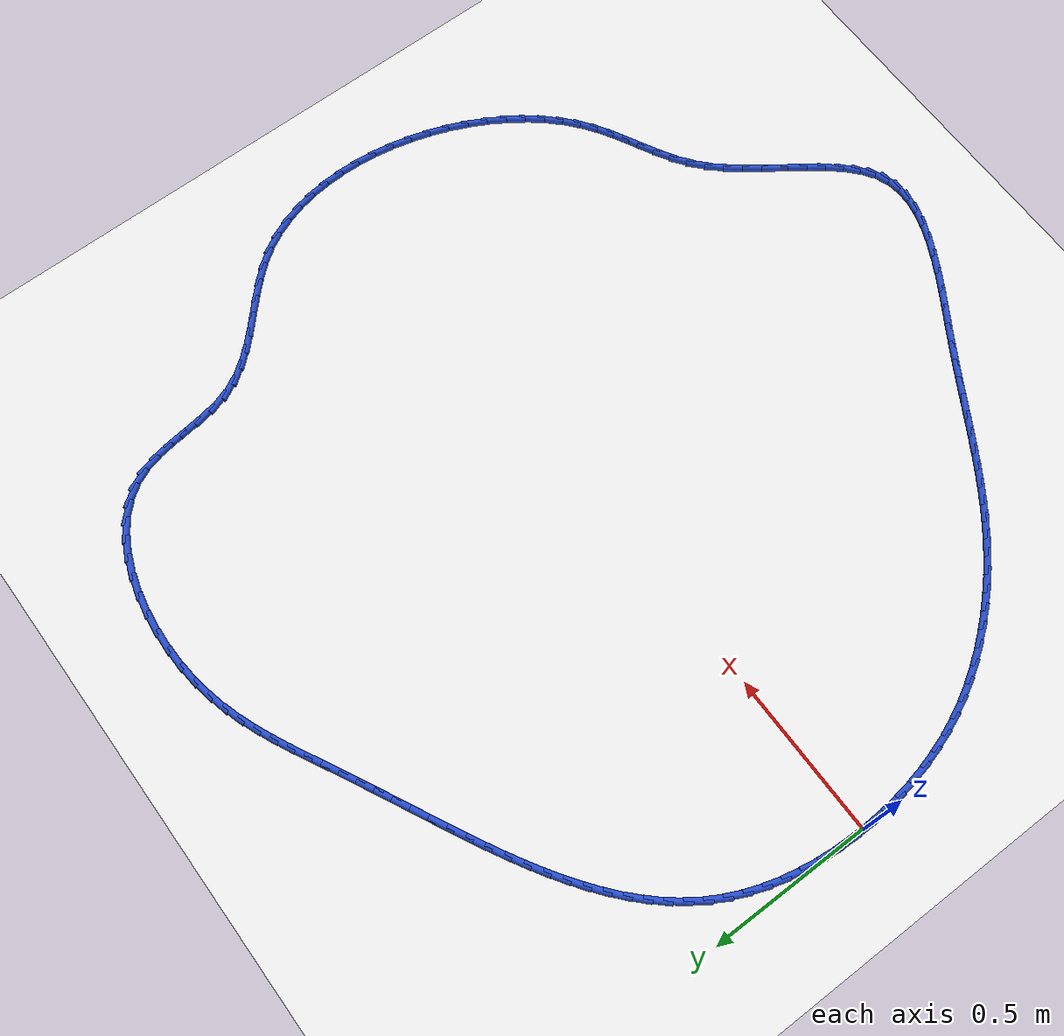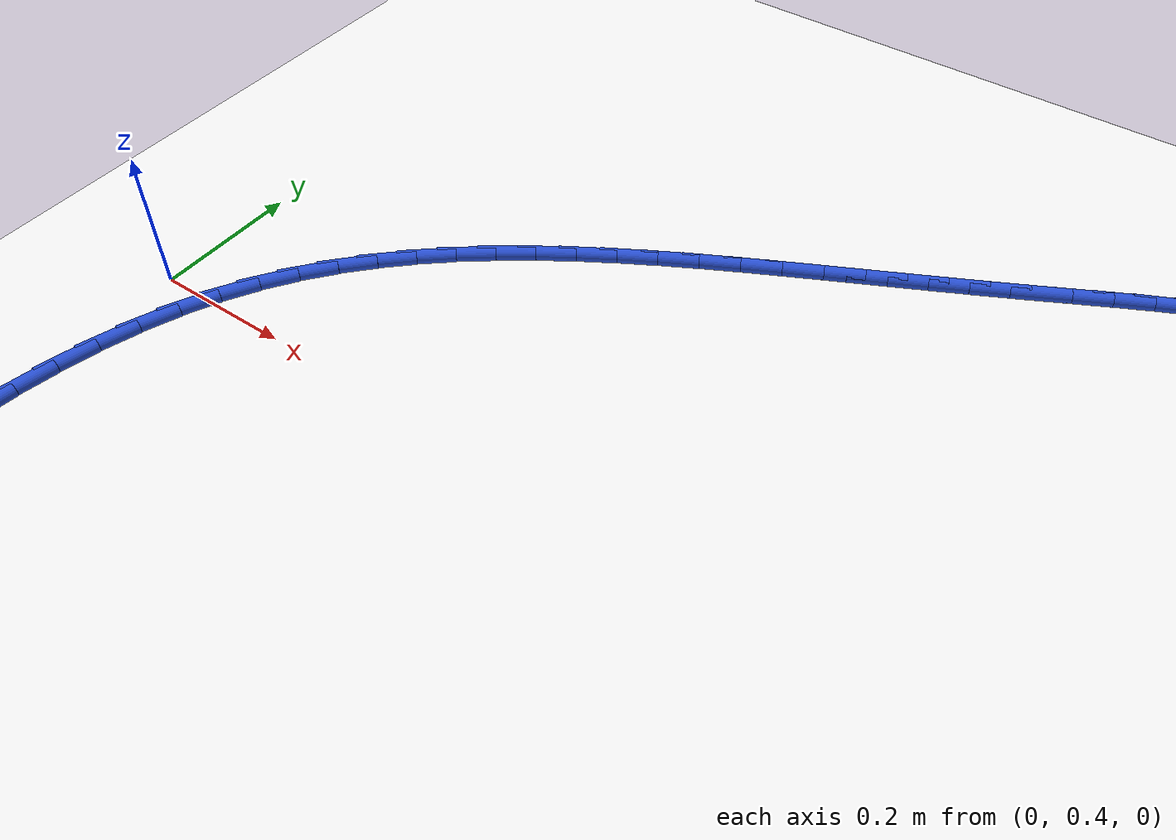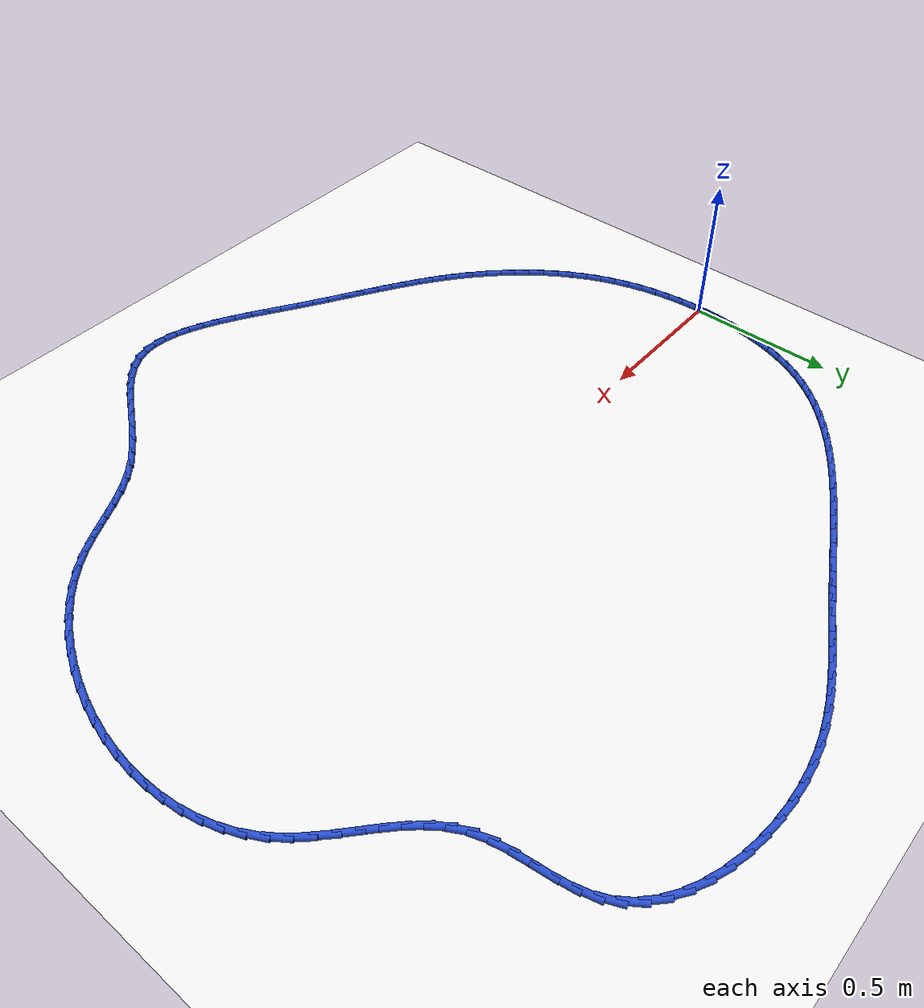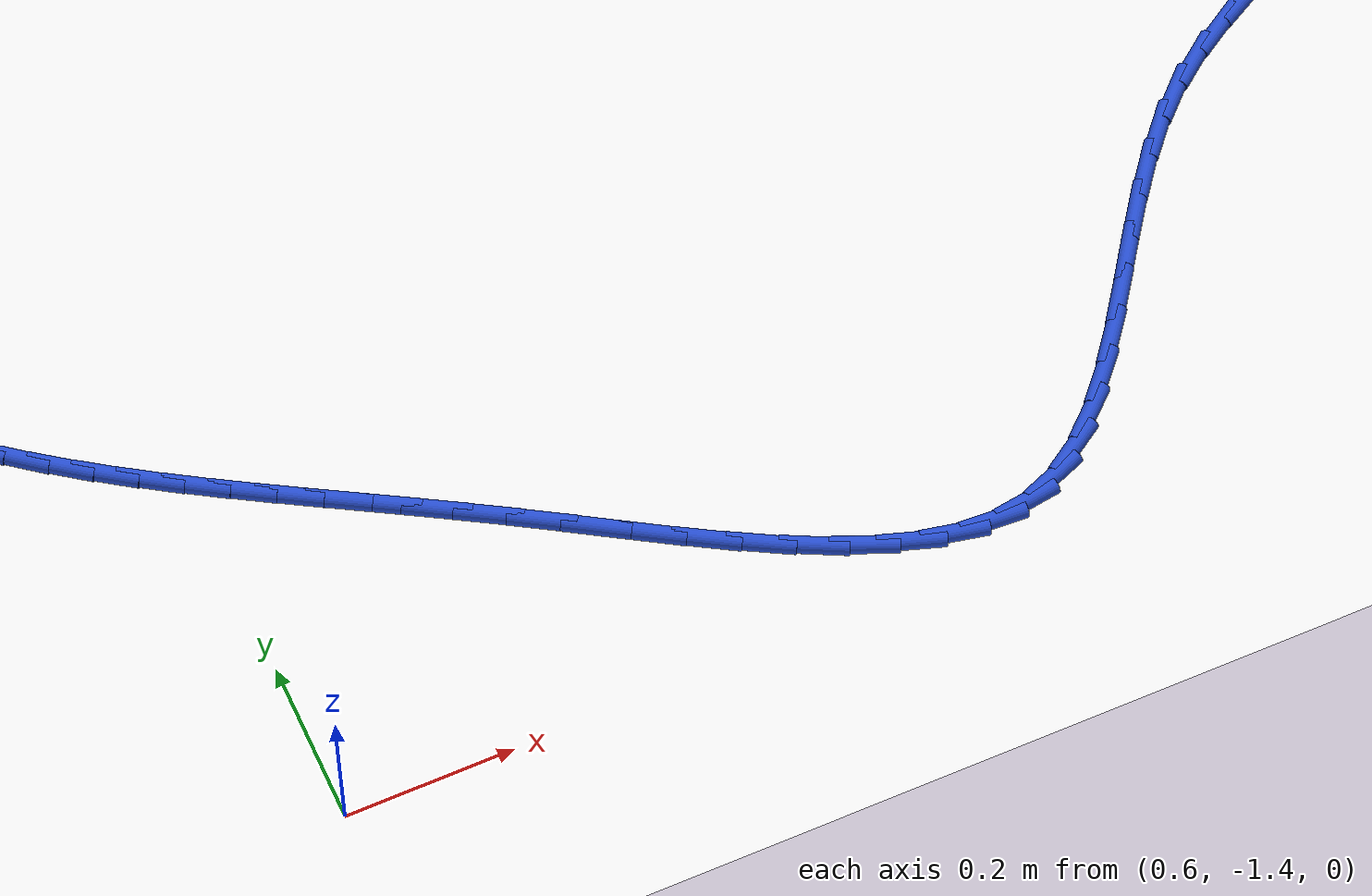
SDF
<sdf version="1.6">
 <world name="default">
  <light name="sun" type="directional">
   <pose>0 0 10 0 -0 0</pose>
   <diffuse>0.8 0.8 0.8 1</diffuse>
   <specular>0.2 0.2 0.2 1</specular>
   <attenuation>
    <range>1000</range>
    <constant>0.9</constant>
    <linear>0.01</linear>
    <quadratic>0.001</quadratic>
   </attenuation>
   <direction>-0.5 0.1 -0.9</direction>
  </light>
  <model name="ground_plane">
   <static>1</static>
   <link name="link">
    <collision name="collision">
     <geometry><plane><normal>0 0 1</normal><size>100 100</size></plane></geometry>
     <surface><friction><ode><mu>100</mu><mu2>50</mu2></ode></friction></surface>
    </collision>
    <visual name="visual">
     <cast_shadows>0</cast_shadows>
     <geometry><plane><normal>0 0 1</normal><size>100 100</size></plane></geometry>
     <material>
      <script><uri>file://media/materials/scripts/gazebo.material</uri><name>Gazebo/WhiteGlow</name></script>
     </material>
    </visual>
   </link>
  </model>
  <gravity>0 0 -9.8</gravity>
  <magnetic_field>6e-06 2.3e-05 -4.2e-05</magnetic_field>
  <atmosphere type="adiabatic"/>
  <physics name="default_physics" default="0" type="ode">
   <max_step_size>0.001</max_step_size>
   <real_time_factor>1</real_time_factor>
   <real_time_update_rate>1000</real_time_update_rate>
  </physics>
  <scene><ambient>0.4 0.4 0.4 1</ambient><background>0.7 0.7 0.7 1</background><shadows>1</shadows></scene>
  <spherical_coordinates>
   <surface_model>EARTH_WGS84</surface_model>
   <latitude_deg>0</latitude_deg>
   <longitude_deg>0</longitude_deg>
   <elevation>0</elevation>
   <heading_deg>0</heading_deg>
  </spherical_coordinates>
  <model name="line">
   <link name="link_0">
    <pose>1.734723475976807e-17 8.326672684688674e-17 0.01 0 1.57 1.5549541364422934</pose>
    <collision name="collision">
     <geometry><cylinder><radius>0.01</radius><length>0.08</length></cylinder></geometry>
    </collision>
    <visual name="visual">
     <material>
      <script><name>Gazebo/Blue</name><uri>file://media/materials/scripts/gazebo.material</uri></script>
     </material>
     <geometry><cylinder><radius>0.01</radius><length>0.08</length></cylinder></geometry>
    </visual>
   </link>
   <link name="link_1">
    <pose>0.0008758087973025836 0.05527868987067464 0.01 0 1.57 1.5047198499125114</pose>
    <collision name="collision">
     <geometry><cylinder><radius>0.01</radius><length>0.08</length></cylinder></geometry>
    </collision>
    <visual name="visual">
     <material>
      <script><name>Gazebo/Blue</name><uri>file://media/materials/scripts/gazebo.material</uri></script>
     </material>
     <geometry><cylinder><radius>0.01</radius><length>0.08</length></cylinder></geometry>
    </visual>
   </link>
   <link name="link_2">
    <pose>0.004531912044155926 0.11052952795859491 0.01 0 1.57 1.4516111610505684</pose>
    <collision name="collision">
     <geometry><cylinder><radius>0.01</radius><length>0.08</length></cylinder></geometry>
    </collision>
    <visual name="visual">
     <material>
      <script><name>Gazebo/Blue</name><uri>file://media/materials/scripts/gazebo.material</uri></script>
     </material>
     <geometry><cylinder><radius>0.01</radius><length>0.08</length></cylinder></geometry>
    </visual>
   </link>
   <link name="link_3">
    <pose>0.011103140113664148 0.1654028297701363 0.01 0 1.57 1.3949423976622928</pose>
    <collision name="collision">
     <geometry><cylinder><radius>0.01</radius><length>0.08</length></cylinder></geometry>
    </collision>
    <visual name="visual">
     <material>
      <script><name>Gazebo/Blue</name><uri>file://media/materials/scripts/gazebo.material</uri></script>
     </material>
     <geometry><cylinder><radius>0.01</radius><length>0.08</length></cylinder></geometry>
    </visual>
   </link>
   <link name="link_4">
    <pose>0.0207243233789313 0.2195489108116741 0.01 0 1.57 1.334015802976964</pose>
    <collision name="collision">
     <geometry><cylinder><radius>0.01</radius><length>0.08</length></cylinder></geometry>
    </collision>
    <visual name="visual">
     <material>
      <script><name>Gazebo/Blue</name><uri>file://media/materials/scripts/gazebo.material</uri></script>
     </material>
     <geometry><cylinder><radius>0.01</radius><length>0.08</length></cylinder></geometry>
    </visual>
   </link>
   <link name="link_5">
    <pose>0.03353029221306147 0.272618086589584 0.01 0 1.57 1.2681359281461293</pose>
    <collision name="collision">
     <geometry><cylinder><radius>0.01</radius><length>0.08</length></cylinder></geometry>
    </collision>
    <visual name="visual">
     <material>
      <script><name>Gazebo/Blue</name><uri>file://media/materials/scripts/gazebo.material</uri></script>
     </material>
     <geometry><cylinder><radius>0.01</radius><length>0.08</length></cylinder></geometry>
    </visual>
   </link>
   <link name="link_6">
    <pose>0.04965587698915874 0.32426067261024116 0.01 0 1.57 1.1966417578673731</pose>
    <collision name="collision">
     <geometry><cylinder><radius>0.01</radius><length>0.08</length></cylinder></geometry>
    </collision>
    <visual name="visual">
     <material>
      <script><name>Gazebo/Blue</name><uri>file://media/materials/scripts/gazebo.material</uri></script>
     </material>
     <geometry><cylinder><radius>0.01</radius><length>0.08</length></cylinder></geometry>
    </visual>
   </link>
   <link name="link_7">
    <pose>0.06923590808032719 0.3741269843800211 0.01 0 1.57 1.1189622204853409</pose>
    <collision name="collision">
     <geometry><cylinder><radius>0.01</radius><length>0.08</length></cylinder></geometry>
    </collision>
    <visual name="visual">
     <material>
      <script><name>Gazebo/Blue</name><uri>file://media/materials/scripts/gazebo.material</uri></script>
     </material>
     <geometry><cylinder><radius>0.01</radius><length>0.08</length></cylinder></geometry>
    </visual>
   </link>
   <link name="link_8">
    <pose>0.09240521585967089 0.4218673374052993 0.01 0 1.57 1.0355023423104208</pose>
    <collision name="collision">
     <geometry><cylinder><radius>0.01</radius><length>0.08</length></cylinder></geometry>
    </collision>
    <visual name="visual">
     <material>
      <script><name>Gazebo/Blue</name><uri>file://media/materials/scripts/gazebo.material</uri></script>
     </material>
     <geometry><cylinder><radius>0.01</radius><length>0.08</length></cylinder></geometry>
    </visual>
   </link>
   <link name="link_9">
    <pose>0.11926956722975601 0.46716591893143583 0.01 0 1.57 0.9536512909180558</pose>
    <collision name="collision">
     <geometry><cylinder><radius>0.01</radius><length>0.08</length></cylinder></geometry>
    </collision>
    <visual name="visual">
     <material>
      <script><name>Gazebo/Blue</name><uri>file://media/materials/scripts/gazebo.material</uri></script>
     </material>
     <geometry><cylinder><radius>0.01</radius><length>0.08</length></cylinder></geometry>
    </visual>
   </link>
   <link name="link_10">
    <pose>0.14967324009707733 0.5100116660102791 0.01 0 1.57 0.8780551493363372</pose>
    <collision name="collision">
     <geometry><cylinder><radius>0.01</radius><length>0.08</length></cylinder></geometry>
    </collision>
    <visual name="visual">
     <material>
      <script><name>Gazebo/Blue</name><uri>file://media/materials/scripts/gazebo.material</uri></script>
     </material>
     <geometry><cylinder><radius>0.01</radius><length>0.08</length></cylinder></geometry>
    </visual>
   </link>
   <link name="link_11">
    <pose>0.18332217036943413 0.5505547450301503 0.01 0 1.57 0.8093055608791737</pose>
    <collision name="collision">
     <geometry><cylinder><radius>0.01</radius><length>0.08</length></cylinder></geometry>
    </collision>
    <visual name="visual">
     <material>
      <script><name>Gazebo/Blue</name><uri>file://media/materials/scripts/gazebo.material</uri></script>
     </material>
     <geometry><cylinder><radius>0.01</radius><length>0.08</length></cylinder></geometry>
    </visual>
   </link>
   <link name="link_12">
    <pose>0.21992103538364283 0.5889467891686792 0.01 0 1.57 0.7475975208602883</pose>
    <collision name="collision">
     <geometry><cylinder><radius>0.01</radius><length>0.08</length></cylinder></geometry>
    </collision>
    <visual name="visual">
     <material>
      <script><name>Gazebo/Blue</name><uri>file://media/materials/scripts/gazebo.material</uri></script>
     </material>
     <geometry><cylinder><radius>0.01</radius><length>0.08</length></cylinder></geometry>
    </visual>
   </link>
   <link name="link_13">
    <pose>0.2591745124765196 0.6253394316034943 0.01 0 1.57 0.6928571532560629</pose>
    <collision name="collision">
     <geometry><cylinder><radius>0.01</radius><length>0.08</length></cylinder></geometry>
    </collision>
    <visual name="visual">
     <material>
      <script><name>Gazebo/Blue</name><uri>file://media/materials/scripts/gazebo.material</uri></script>
     </material>
     <geometry><cylinder><radius>0.01</radius><length>0.08</length></cylinder></geometry>
    </visual>
   </link>
   <link name="link_14">
    <pose>0.3007872789848809 0.6598843055122251 0.01 0 1.57 0.6448359671258451</pose>
    <collision name="collision">
     <geometry><cylinder><radius>0.01</radius><length>0.08</length></cylinder></geometry>
    </collision>
    <visual name="visual">
     <material>
      <script><name>Gazebo/Blue</name><uri>file://media/materials/scripts/gazebo.material</uri></script>
     </material>
     <geometry><cylinder><radius>0.01</radius><length>0.08</length></cylinder></geometry>
    </visual>
   </link>
   <link name="link_15">
    <pose>0.3444640122455428 0.6927330440725009 0.01 0 1.57 0.6031913646656466</pose>
    <collision name="collision">
     <geometry><cylinder><radius>0.01</radius><length>0.08</length></cylinder></geometry>
    </collision>
    <visual name="visual">
     <material>
      <script><name>Gazebo/Blue</name><uri>file://media/materials/scripts/gazebo.material</uri></script>
     </material>
     <geometry><cylinder><radius>0.01</radius><length>0.08</length></cylinder></geometry>
    </visual>
   </link>
   <link name="link_16">
    <pose>0.38990938959532184 0.7240372804619511 0.01 0 1.57 0.5675481863297864</pose>
    <collision name="collision">
     <geometry><cylinder><radius>0.01</radius><length>0.08</length></cylinder></geometry>
    </collision>
    <visual name="visual">
     <material>
      <script><name>Gazebo/Blue</name><uri>file://media/materials/scripts/gazebo.material</uri></script>
     </material>
     <geometry><cylinder><radius>0.01</radius><length>0.08</length></cylinder></geometry>
    </visual>
   </link>
   <link name="link_17">
    <pose>0.4368280883710341 0.7539486478582047 0.01 0 1.57 0.5375421657477882</pose>
    <collision name="collision">
     <geometry><cylinder><radius>0.01</radius><length>0.08</length></cylinder></geometry>
    </collision>
    <visual name="visual">
     <material>
      <script><name>Gazebo/Blue</name><uri>file://media/materials/scripts/gazebo.material</uri></script>
     </material>
     <geometry><cylinder><radius>0.01</radius><length>0.08</length></cylinder></geometry>
    </visual>
   </link>
   <link name="link_18">
    <pose>0.48492478590949595 0.7826187794388908 0.01 0 1.57 0.5128489066966759</pose>
    <collision name="collision">
     <geometry><cylinder><radius>0.01</radius><length>0.08</length></cylinder></geometry>
    </collision>
    <visual name="visual">
     <material>
      <script><name>Gazebo/Blue</name><uri>file://media/materials/scripts/gazebo.material</uri></script>
     </material>
     <geometry><cylinder><radius>0.01</radius><length>0.08</length></cylinder></geometry>
    </visual>
   </link>
   <link name="link_19">
    <pose>0.5339041595475238 0.810199308381639 0.01 0 1.57 0.49320260165248964</pose>
    <collision name="collision">
     <geometry><cylinder><radius>0.01</radius><length>0.08</length></cylinder></geometry>
    </collision>
    <visual name="visual">
     <material>
      <script><name>Gazebo/Blue</name><uri>file://media/materials/scripts/gazebo.material</uri></script>
     </material>
     <geometry><cylinder><radius>0.01</radius><length>0.08</length></cylinder></geometry>
    </visual>
   </link>
   <link name="link_20">
    <pose>0.5834708866219338 0.8368418678640781 0.01 0 1.57 0.478408290178742</pose>
    <collision name="collision">
     <geometry><cylinder><radius>0.01</radius><length>0.08</length></cylinder></geometry>
    </collision>
    <visual name="visual">
     <material>
      <script><name>Gazebo/Blue</name><uri>file://media/materials/scripts/gazebo.material</uri></script>
     </material>
     <geometry><cylinder><radius>0.01</radius><length>0.08</length></cylinder></geometry>
    </visual>
   </link>
   <link name="link_21">
    <pose>0.6333296444695424 0.8626980910638377 0.01 0 1.57 0.46835070967737275</pose>
    <collision name="collision">
     <geometry><cylinder><radius>0.01</radius><length>0.08</length></cylinder></geometry>
    </collision>
    <visual name="visual">
     <material>
      <script><name>Gazebo/Blue</name><uri>file://media/materials/scripts/gazebo.material</uri></script>
     </material>
     <geometry><cylinder><radius>0.01</radius><length>0.08</length></cylinder></geometry>
    </visual>
   </link>
   <link name="link_22">
    <pose>0.6831851104271658 0.8879196111585468 0.01 0 1.57 0.4630003723994389</pose>
    <collision name="collision">
     <geometry><cylinder><radius>0.01</radius><length>0.08</length></cylinder></geometry>
    </collision>
    <visual name="visual">
     <material>
      <script><name>Gazebo/Blue</name><uri>file://media/materials/scripts/gazebo.material</uri></script>
     </material>
     <geometry><cylinder><radius>0.01</radius><length>0.08</length></cylinder></geometry>
    </visual>
   </link>
   <link name="link_23">
    <pose>0.7327421398714512 0.9126580449418787 0.01 0 1.57 0.46160993479304074</pose>
    <collision name="collision">
     <geometry><cylinder><radius>0.01</radius><length>0.08</length></cylinder></geometry>
    </collision>
    <visual name="visual">
     <material>
      <script><name>Gazebo/Blue</name><uri>file://media/materials/scripts/gazebo.material</uri></script>
     </material>
     <geometry><cylinder><radius>0.01</radius><length>0.08</length></cylinder></geometry>
    </visual>
   </link>
   <link name="link_24">
    <pose>0.7817901166250218 0.937057230553153 0.01 0 1.57 0.4621584505705805</pose>
    <collision name="collision">
     <geometry><cylinder><radius>0.01</radius><length>0.08</length></cylinder></geometry>
    </collision>
    <visual name="visual">
     <material>
      <script><name>Gazebo/Blue</name><uri>file://media/materials/scripts/gazebo.material</uri></script>
     </material>
     <geometry><cylinder><radius>0.01</radius><length>0.08</length></cylinder></geometry>
    </visual>
   </link>
   <link name="link_25">
    <pose>0.8303378811273123 0.9612408108335463 0.01 0 1.57 0.46435616678150154</pose>
    <collision name="collision">
     <geometry><cylinder><radius>0.01</radius><length>0.08</length></cylinder></geometry>
    </collision>
    <visual name="visual">
     <material>
      <script><name>Gazebo/Blue</name><uri>file://media/materials/scripts/gazebo.material</uri></script>
     </material>
     <geometry><cylinder><radius>0.01</radius><length>0.08</length></cylinder></geometry>
    </visual>
   </link>
   <link name="link_26">
    <pose>0.8784294274430855 0.9853291936434235 0.01 0 1.57 0.4682332799169837</pose>
    <collision name="collision">
     <geometry><cylinder><radius>0.01</radius><length>0.08</length></cylinder></geometry>
    </collision>
    <visual name="visual">
     <material>
      <script><name>Gazebo/Blue</name><uri>file://media/materials/scripts/gazebo.material</uri></script>
     </material>
     <geometry><cylinder><radius>0.01</radius><length>0.08</length></cylinder></geometry>
    </visual>
   </link>
   <link name="link_27">
    <pose>0.9261087496371038 1.0094427868431497 0.01 0 1.57 0.4738030185185685</pose>
    <collision name="collision">
     <geometry><cylinder><radius>0.01</radius><length>0.08</length></cylinder></geometry>
    </collision>
    <visual name="visual">
     <material>
      <script><name>Gazebo/Blue</name><uri>file://media/materials/scripts/gazebo.material</uri></script>
     </material>
     <geometry><cylinder><radius>0.01</radius><length>0.08</length></cylinder></geometry>
    </visual>
   </link>
   <link name="link_28">
    <pose>0.9734198417741309 1.033701998293091 0.01 0 1.57 0.48000184230579357</pose>
    <collision name="collision">
     <geometry><cylinder><radius>0.01</radius><length>0.08</length></cylinder></geometry>
    </collision>
    <visual name="visual">
     <material>
      <script><name>Gazebo/Blue</name><uri>file://media/materials/scripts/gazebo.material</uri></script>
     </material>
     <geometry><cylinder><radius>0.01</radius><length>0.08</length></cylinder></geometry>
    </visual>
   </link>
   <link name="link_29">
    <pose>1.0204329722901042 1.0581776539468464 0.01 0 1.57 0.47834226492540677</pose>
    <collision name="collision">
     <geometry><cylinder><radius>0.01</radius><length>0.08</length></cylinder></geometry>
    </collision>
    <visual name="visual">
     <material>
      <script><name>Gazebo/Blue</name><uri>file://media/materials/scripts/gazebo.material</uri></script>
     </material>
     <geometry><cylinder><radius>0.01</radius><length>0.08</length></cylinder></geometry>
    </visual>
   </link>
   <link name="link_30">
    <pose>1.0674280937597411 1.0825448884834374 0.01 0 1.57 0.4647573889563969</pose>
    <collision name="collision">
     <geometry><cylinder><radius>0.01</radius><length>0.08</length></cylinder></geometry>
    </collision>
    <visual name="visual">
     <material>
      <script><name>Gazebo/Blue</name><uri>file://media/materials/scripts/gazebo.material</uri></script>
     </material>
     <geometry><cylinder><radius>0.01</radius><length>0.08</length></cylinder></geometry>
    </visual>
   </link>
   <link name="link_31">
    <pose>1.114785567364077 1.1062893572552939 0.01 0 1.57 0.43934025167964447</pose>
    <collision name="collision">
     <geometry><cylinder><radius>0.01</radius><length>0.08</length></cylinder></geometry>
    </collision>
    <visual name="visual">
     <material>
      <script><name>Gazebo/Blue</name><uri>file://media/materials/scripts/gazebo.material</uri></script>
     </material>
     <geometry><cylinder><radius>0.01</radius><length>0.08</length></cylinder></geometry>
    </visual>
   </link>
   <link name="link_32">
    <pose>1.162886383175069 1.128895528845775 0.01 0 1.57 0.4024152046235309</pose>
    <collision name="collision">
     <geometry><cylinder><radius>0.01</radius><length>0.08</length></cylinder></geometry>
    </collision>
    <visual name="visual">
     <material>
      <script><name>Gazebo/Blue</name><uri>file://media/materials/scripts/gazebo.material</uri></script>
     </material>
     <geometry><cylinder><radius>0.01</radius><length>0.08</length></cylinder></geometry>
    </visual>
   </link>
   <link name="link_33">
    <pose>1.2121115312646746 1.1498478718382399 0.01 0 1.57 0.35460025331843054</pose>
    <collision name="collision">
     <geometry><cylinder><radius>0.01</radius><length>0.08</length></cylinder></geometry>
    </collision>
    <visual name="visual">
     <material>
      <script><name>Gazebo/Blue</name><uri>file://media/materials/scripts/gazebo.material</uri></script>
     </material>
     <geometry><cylinder><radius>0.01</radius><length>0.08</length></cylinder></geometry>
    </visual>
   </link>
   <link name="link_34">
    <pose>1.2628420017048514 1.1686308548160476 0.01 0 1.57 0.2969063025820413</pose>
    <collision name="collision">
     <geometry><cylinder><radius>0.01</radius><length>0.08</length></cylinder></geometry>
    </collision>
    <visual name="visual">
     <material>
      <script><name>Gazebo/Blue</name><uri>file://media/materials/scripts/gazebo.material</uri></script>
     </material>
     <geometry><cylinder><radius>0.01</radius><length>0.08</length></cylinder></geometry>
    </visual>
   </link>
   <link name="link_35">
    <pose>1.3154587845675563 1.184728946362557 0.01 0 1.57 0.23081038291306477</pose>
    <collision name="collision">
     <geometry><cylinder><radius>0.01</radius><length>0.08</length></cylinder></geometry>
    </collision>
    <visual name="visual">
     <material>
      <script><name>Gazebo/Blue</name><uri>file://media/materials/scripts/gazebo.material</uri></script>
     </material>
     <geometry><cylinder><radius>0.01</radius><length>0.08</length></cylinder></geometry>
    </visual>
   </link>
   <link name="link_36">
    <pose>1.3703428699247466 1.1976266150611272 0.01 0 1.57 0.1584560932622686</pose>
    <collision name="collision">
     <geometry><cylinder><radius>0.01</radius><length>0.08</length></cylinder></geometry>
    </collision>
    <visual name="visual">
     <material>
      <script><name>Gazebo/Blue</name><uri>file://media/materials/scripts/gazebo.material</uri></script>
     </material>
     <geometry><cylinder><radius>0.01</radius><length>0.08</length></cylinder></geometry>
    </visual>
   </link>
   <link name="link_37">
    <pose>1.4278493617497325 1.2068159074114269 0.01 0 1.57 0.08603720980987684</pose>
    <collision name="collision">
     <geometry><cylinder><radius>0.01</radius><length>0.08</length></cylinder></geometry>
    </collision>
    <visual name="visual">
     <material>
      <script><name>Gazebo/Blue</name><uri>file://media/materials/scripts/gazebo.material</uri></script>
     </material>
     <geometry><cylinder><radius>0.01</radius><length>0.08</length></cylinder></geometry>
    </visual>
   </link>
   <link name="link_38">
    <pose>1.4876901010338748 1.2119771792102536 0.01 0 1.57 0.016498323912422754</pose>
    <collision name="collision">
     <geometry><cylinder><radius>0.01</radius><length>0.08</length></cylinder></geometry>
    </collision>
    <visual name="visual">
     <material>
      <script><name>Gazebo/Blue</name><uri>file://media/materials/scripts/gazebo.material</uri></script>
     </material>
     <geometry><cylinder><radius>0.01</radius><length>0.08</length></cylinder></geometry>
    </visual>
   </link>
   <link name="link_39">
    <pose>1.5489058831649645 1.2129872286574337 0.01 0 1.57 -0.05279440181231193</pose>
    <collision name="collision">
     <geometry><cylinder><radius>0.01</radius><length>0.08</length></cylinder></geometry>
    </collision>
    <visual name="visual">
     <material>
      <script><name>Gazebo/Blue</name><uri>file://media/materials/scripts/gazebo.material</uri></script>
     </material>
     <geometry><cylinder><radius>0.01</radius><length>0.08</length></cylinder></geometry>
    </visual>
   </link>
   <link name="link_40">
    <pose>1.6105060577933654 1.2097320594020065 0.01 0 1.57 -0.12451875571283302</pose>
    <collision name="collision">
     <geometry><cylinder><radius>0.01</radius><length>0.08</length></cylinder></geometry>
    </collision>
    <visual name="visual">
     <material>
      <script><name>Gazebo/Blue</name><uri>file://media/materials/scripts/gazebo.material</uri></script>
     </material>
     <geometry><cylinder><radius>0.01</radius><length>0.08</length></cylinder></geometry>
    </visual>
   </link>
   <link name="link_41">
    <pose>1.6714999745694434 1.202097675093012 0.01 0 1.57 -0.20141015896901712</pose>
    <collision name="collision">
     <geometry><cylinder><radius>0.01</radius><length>0.08</length></cylinder></geometry>
    </collision>
    <visual name="visual">
     <material>
      <script><name>Gazebo/Blue</name><uri>file://media/materials/scripts/gazebo.material</uri></script>
     </material>
     <geometry><cylinder><radius>0.01</radius><length>0.08</length></cylinder></geometry>
    </visual>
   </link>
   <link name="link_42">
    <pose>1.7308969831435637 1.1899700793794903 0.01 0 1.57 -0.2864749162294685</pose>
    <collision name="collision">
     <geometry><cylinder><radius>0.01</radius><length>0.08</length></cylinder></geometry>
    </collision>
    <visual name="visual">
     <material>
      <script><name>Gazebo/Blue</name><uri>file://media/materials/scripts/gazebo.material</uri></script>
     </material>
     <geometry><cylinder><radius>0.01</radius><length>0.08</length></cylinder></geometry>
    </visual>
   </link>
   <link name="link_43">
    <pose>1.7877064331660917 1.1732352759104812 0.01 0 1.57 -0.3831515980471236</pose>
    <collision name="collision">
     <geometry><cylinder><radius>0.01</radius><length>0.08</length></cylinder></geometry>
    </collision>
    <visual name="visual">
     <material>
      <script><name>Gazebo/Blue</name><uri>file://media/materials/scripts/gazebo.material</uri></script>
     </material>
     <geometry><cylinder><radius>0.01</radius><length>0.08</length></cylinder></geometry>
    </visual>
   </link>
   <link name="link_44">
    <pose>1.8409376742873922 1.1517792683350245 0.01 0 1.57 -0.49534837484774535</pose>
    <collision name="collision">
     <geometry><cylinder><radius>0.01</radius><length>0.08</length></cylinder></geometry>
    </collision>
    <visual name="visual">
     <material>
      <script><name>Gazebo/Blue</name><uri>file://media/materials/scripts/gazebo.material</uri></script>
     </material>
     <geometry><cylinder><radius>0.01</radius><length>0.08</length></cylinder></geometry>
    </visual>
   </link>
   <link name="link_45">
    <pose>1.8896000561578299 1.1254880603021602 0.01 0 1.57 -0.6271686142967373</pose>
    <collision name="collision">
     <geometry><cylinder><radius>0.01</radius><length>0.08</length></cylinder></geometry>
    </collision>
    <visual name="visual">
     <material>
      <script><name>Gazebo/Blue</name><uri>file://media/materials/scripts/gazebo.material</uri></script>
     </material>
     <geometry><cylinder><radius>0.01</radius><length>0.08</length></cylinder></geometry>
    </visual>
   </link>
   <link name="link_46">
    <pose>1.9327029284277712 1.0942476554609284 0.01 0 1.57 -0.7819789215042338</pose>
    <collision name="collision">
     <geometry><cylinder><radius>0.01</radius><length>0.08</length></cylinder></geometry>
    </collision>
    <visual name="visual">
     <material>
      <script><name>Gazebo/Blue</name><uri>file://media/materials/scripts/gazebo.material</uri></script>
     </material>
     <geometry><cylinder><radius>0.01</radius><length>0.08</length></cylinder></geometry>
    </visual>
   </link>
   <link name="link_47">
    <pose>1.9692556407475803 1.057944057460369 0.01 0 1.57 -0.96046928759951</pose>
    <collision name="collision">
     <geometry><cylinder><radius>0.01</radius><length>0.08</length></cylinder></geometry>
    </collision>
    <visual name="visual">
     <material>
      <script><name>Gazebo/Blue</name><uri>file://media/materials/scripts/gazebo.material</uri></script>
     </material>
     <geometry><cylinder><radius>0.01</radius><length>0.08</length></cylinder></geometry>
    </visual>
   </link>
   <link name="link_48">
    <pose>1.9982675427676229 1.0164632699495213 0.01 0 1.57 -1.155850809281119</pose>
    <collision name="collision">
     <geometry><cylinder><radius>0.01</radius><length>0.08</length></cylinder></geometry>
    </collision>
    <visual name="visual">
     <material>
      <script><name>Gazebo/Blue</name><uri>file://media/materials/scripts/gazebo.material</uri></script>
     </material>
     <geometry><cylinder><radius>0.01</radius><length>0.08</length></cylinder></geometry>
    </visual>
   </link>
   <link name="link_49">
    <pose>2.0188510142915383 0.9697382625432132 0.01 0 1.57 -1.3183940002396877</pose>
    <collision name="collision">
     <geometry><cylinder><radius>0.01</radius><length>0.08</length></cylinder></geometry>
    </collision>
    <visual name="visual">
     <material>
      <script><name>Gazebo/Blue</name><uri>file://media/materials/scripts/gazebo.material</uri></script>
     </material>
     <geometry><cylinder><radius>0.01</radius><length>0.08</length></cylinder></geometry>
    </visual>
   </link>
   <link name="link_50">
    <pose>2.032044819382666 0.9185801409587488 0.01 0 1.57 -1.413750732601165</pose>
    <collision name="collision">
     <geometry><cylinder><radius>0.01</radius><length>0.08</length></cylinder></geometry>
    </collision>
    <visual name="visual">
     <material>
      <script><name>Gazebo/Blue</name><uri>file://media/materials/scripts/gazebo.material</uri></script>
     </material>
     <geometry><cylinder><radius>0.01</radius><length>0.08</length></cylinder></geometry>
    </visual>
   </link>
   <link name="link_51">
    <pose>2.040595924797375 0.8645786896466844 0.01 0 1.57 -1.4498110701978522</pose>
    <collision name="collision">
     <geometry><cylinder><radius>0.01</radius><length>0.08</length></cylinder></geometry>
    </collision>
    <visual name="visual">
     <material>
      <script><name>Gazebo/Blue</name><uri>file://media/materials/scripts/gazebo.material</uri></script>
     </material>
     <geometry><cylinder><radius>0.01</radius><length>0.08</length></cylinder></geometry>
    </visual>
   </link>
   <link name="link_52">
    <pose>2.0473104933910493 0.8093506774099489 0.01 0 1.57 -1.4315769445248943</pose>
    <collision name="collision">
     <geometry><cylinder><radius>0.01</radius><length>0.08</length></cylinder></geometry>
    </collision>
    <visual name="visual">
     <material>
      <script><name>Gazebo/Blue</name><uri>file://media/materials/scripts/gazebo.material</uri></script>
     </material>
     <geometry><cylinder><radius>0.01</radius><length>0.08</length></cylinder></geometry>
    </visual>
   </link>
   <link name="link_53">
    <pose>2.054994688019075 0.754512873051474 0.01 0 1.57 -1.3571871627185286</pose>
    <collision name="collision">
     <geometry><cylinder><radius>0.01</radius><length>0.08</length></cylinder></geometry>
    </collision>
    <visual name="visual">
     <material>
      <script><name>Gazebo/Blue</name><uri>file://media/materials/scripts/gazebo.material</uri></script>
     </material>
     <geometry><cylinder><radius>0.01</radius><length>0.08</length></cylinder></geometry>
    </visual>
   </link>
   <link name="link_54">
    <pose>2.0664546715368384 0.7016820453741899 0.01 0 1.57 -1.2200794172710414</pose>
    <collision name="collision">
     <geometry><cylinder><radius>0.01</radius><length>0.08</length></cylinder></geometry>
    </collision>
    <visual name="visual">
     <material>
      <script><name>Gazebo/Blue</name><uri>file://media/materials/scripts/gazebo.material</uri></script>
     </material>
     <geometry><cylinder><radius>0.01</radius><length>0.08</length></cylinder></geometry>
    </visual>
   </link>
   <link name="link_55">
    <pose>2.0844637119460048 0.6524556508415957 0.01 0 1.57 -1.0530897019441856</pose>
    <collision name="collision">
     <geometry><cylinder><radius>0.01</radius><length>0.08</length></cylinder></geometry>
    </collision>
    <visual name="visual">
     <material>
      <script><name>Gazebo/Blue</name><uri>file://media/materials/scripts/gazebo.material</uri></script>
     </material>
     <geometry><cylinder><radius>0.01</radius><length>0.08</length></cylinder></geometry>
    </visual>
   </link>
   <link name="link_56">
    <pose>2.110102505828461 0.6074374490293374 0.01 0 1.57 -0.9176567154819267</pose>
    <collision name="collision">
     <geometry><cylinder><radius>0.01</radius><length>0.08</length></cylinder></geometry>
    </collision>
    <visual name="visual">
     <material>
      <script><name>Gazebo/Blue</name><uri>file://media/materials/scripts/gazebo.material</uri></script>
     </material>
     <geometry><cylinder><radius>0.01</radius><length>0.08</length></cylinder></geometry>
    </visual>
   </link>
   <link name="link_57">
    <pose>2.141978280617027 0.5657790430091059 0.01 0 1.57 -0.821514991020112</pose>
    <collision name="collision">
     <geometry><cylinder><radius>0.01</radius><length>0.08</length></cylinder></geometry>
    </collision>
    <visual name="visual">
     <material>
      <script><name>Gazebo/Blue</name><uri>file://media/materials/scripts/gazebo.material</uri></script>
     </material>
     <geometry><cylinder><radius>0.01</radius><length>0.08</length></cylinder></geometry>
    </visual>
   </link>
   <link name="link_58">
    <pose>2.1785021085780705 0.5265168745210467 0.01 0 1.57 -0.7627511012854855</pose>
    <collision name="collision">
     <geometry><cylinder><radius>0.01</radius><length>0.08</length></cylinder></geometry>
    </collision>
    <visual name="visual">
     <material>
      <script><name>Gazebo/Blue</name><uri>file://media/materials/scripts/gazebo.material</uri></script>
     </material>
     <geometry><cylinder><radius>0.01</radius><length>0.08</length></cylinder></geometry>
    </visual>
   </link>
   <link name="link_59">
    <pose>2.218085061977962 0.4886873853053048 0.01 0 1.57 -0.7383392303276833</pose>
    <collision name="collision">
     <geometry><cylinder><radius>0.01</radius><length>0.08</length></cylinder></geometry>
    </collision>
    <visual name="visual">
     <material>
      <script><name>Gazebo/Blue</name><uri>file://media/materials/scripts/gazebo.material</uri></script>
     </material>
     <geometry><cylinder><radius>0.01</radius><length>0.08</length></cylinder></geometry>
    </visual>
   </link>
   <link name="link_60">
    <pose>2.2591382130830704 0.4513270171020263 0.01 0 1.57 -0.7463312899429972</pose>
    <collision name="collision">
     <geometry><cylinder><radius>0.01</radius><length>0.08</length></cylinder></geometry>
    </collision>
    <visual name="visual">
     <material>
      <script><name>Gazebo/Blue</name><uri>file://media/materials/scripts/gazebo.material</uri></script>
     </material>
     <geometry><cylinder><radius>0.01</radius><length>0.08</length></cylinder></geometry>
    </visual>
   </link>
   <link name="link_61">
    <pose>2.300072634159765 0.41347221165135584 0.01 0 1.57 -0.7864936317724981</pose>
    <collision name="collision">
     <geometry><cylinder><radius>0.01</radius><length>0.08</length></cylinder></geometry>
    </collision>
    <visual name="visual">
     <material>
      <script><name>Gazebo/Blue</name><uri>file://media/materials/scripts/gazebo.material</uri></script>
     </material>
     <geometry><cylinder><radius>0.01</radius><length>0.08</length></cylinder></geometry>
    </visual>
   </link>
   <link name="link_62">
    <pose>2.339299397474414 0.3741594106934395 0.01 0 1.57 -0.8599934390843179</pose>
    <collision name="collision">
     <geometry><cylinder><radius>0.01</radius><length>0.08</length></cylinder></geometry>
    </collision>
    <visual name="visual">
     <material>
      <script><name>Gazebo/Blue</name><uri>file://media/materials/scripts/gazebo.material</uri></script>
     </material>
     <geometry><cylinder><radius>0.01</radius><length>0.08</length></cylinder></geometry>
    </visual>
   </link>
   <link name="link_63">
    <pose>2.3752295752933867 0.332425055968422 0.01 0 1.57 -0.9661852743838006</pose>
    <collision name="collision">
     <geometry><cylinder><radius>0.01</radius><length>0.08</length></cylinder></geometry>
    </collision>
    <visual name="visual">
     <material>
      <script><name>Gazebo/Blue</name><uri>file://media/materials/scripts/gazebo.material</uri></script>
     </material>
     <geometry><cylinder><radius>0.01</radius><length>0.08</length></cylinder></geometry>
    </visual>
   </link>
   <link name="link_64">
    <pose>2.406357687441986 0.2873724100060042 0.01 0 1.57 -1.081364535669492</pose>
    <collision name="collision">
     <geometry><cylinder><radius>0.01</radius><length>0.08</length></cylinder></geometry>
    </collision>
    <visual name="visual">
     <material>
      <script><name>Gazebo/Blue</name><uri>file://media/materials/scripts/gazebo.material</uri></script>
     </material>
     <geometry><cylinder><radius>0.01</radius><length>0.08</length></cylinder></geometry>
    </visual>
   </link>
   <link name="link_65">
    <pose>2.4321752760070114 0.2389031027844836 0.01 0 1.57 -1.1890953010450411</pose>
    <collision name="collision">
     <geometry><cylinder><radius>0.01</radius><length>0.08</length></cylinder></geometry>
    </collision>
    <visual name="visual">
     <material>
      <script><name>Gazebo/Blue</name><uri>file://media/materials/scripts/gazebo.material</uri></script>
     </material>
     <geometry><cylinder><radius>0.01</radius><length>0.08</length></cylinder></geometry>
    </visual>
   </link>
   <link name="link_66">
    <pose>2.452830153030504 0.1874442736814856 0.01 0 1.57 -1.2887431031602288</pose>
    <collision name="collision">
     <geometry><cylinder><radius>0.01</radius><length>0.08</length></cylinder></geometry>
    </collision>
    <visual name="visual">
     <material>
      <script><name>Gazebo/Blue</name><uri>file://media/materials/scripts/gazebo.material</uri></script>
     </material>
     <geometry><cylinder><radius>0.01</radius><length>0.08</length></cylinder></geometry>
    </visual>
   </link>
   <link name="link_67">
    <pose>2.468481668968896 0.13343230148163282 0.01 0 1.57 -1.3805758074471217</pose>
    <collision name="collision">
     <geometry><cylinder><radius>0.01</radius><length>0.08</length></cylinder></geometry>
    </collision>
    <visual name="visual">
     <material>
      <script><name>Gazebo/Blue</name><uri>file://media/materials/scripts/gazebo.material</uri></script>
     </material>
     <geometry><cylinder><radius>0.01</radius><length>0.08</length></cylinder></geometry>
    </visual>
   </link>
   <link name="link_68">
    <pose>2.479289174278617 0.0773035649695458 0.01 0 1.57 -1.4652748705228138</pose>
    <collision name="collision">
     <geometry><cylinder><radius>0.01</radius><length>0.08</length></cylinder></geometry>
    </collision>
    <visual name="visual">
     <material>
      <script><name>Gazebo/Blue</name><uri>file://media/materials/scripts/gazebo.material</uri></script>
     </material>
     <geometry><cylinder><radius>0.01</radius><length>0.08</length></cylinder></geometry>
    </visual>
   </link>
   <link name="link_69">
    <pose>2.4854120194160982 0.019494442929847082 0.01 0 1.57 -1.543750412157234</pose>
    <collision name="collision">
     <geometry><cylinder><radius>0.01</radius><length>0.08</length></cylinder></geometry>
    </collision>
    <visual name="visual">
     <material>
      <script><name>Gazebo/Blue</name><uri>file://media/materials/scripts/gazebo.material</uri></script>
     </material>
     <geometry><cylinder><radius>0.01</radius><length>0.08</length></cylinder></geometry>
    </visual>
   </link>
   <link name="link_70">
    <pose>2.487009554837773 -0.039558685852842695 0.01 0 1.57 1.5245815315321705</pose>
    <collision name="collision">
     <geometry><cylinder><radius>0.01</radius><length>0.08</length></cylinder></geometry>
    </collision>
    <visual name="visual">
     <material>
      <script><name>Gazebo/Blue</name><uri>file://media/materials/scripts/gazebo.material</uri></script>
     </material>
     <geometry><cylinder><radius>0.01</radius><length>0.08</length></cylinder></geometry>
    </visual>
   </link>
   <link name="link_71">
    <pose>2.484241131000071 -0.09941944259390101 0.01 0 1.57 1.455507088413543</pose>
    <collision name="collision">
     <geometry><cylinder><radius>0.01</radius><length>0.08</length></cylinder></geometry>
    </collision>
    <visual name="visual">
     <material>
      <script><name>Gazebo/Blue</name><uri>file://media/materials/scripts/gazebo.material</uri></script>
     </material>
     <geometry><cylinder><radius>0.01</radius><length>0.08</length></cylinder></geometry>
    </visual>
   </link>
   <link name="link_72">
    <pose>2.4772660983594244 -0.1596514485087068 0.01 0 1.57 1.3896100677225793</pose>
    <collision name="collision">
     <geometry><cylinder><radius>0.01</radius><length>0.08</length></cylinder></geometry>
    </collision>
    <visual name="visual">
     <material>
      <script><name>Gazebo/Blue</name><uri>file://media/materials/scripts/gazebo.material</uri></script>
     </material>
     <geometry><cylinder><radius>0.01</radius><length>0.08</length></cylinder></geometry>
    </visual>
   </link>
   <link name="link_73">
    <pose>2.466243807372263 -0.2198183248126394 0.01 0 1.57 1.3259145688125686</pose>
    <collision name="collision">
     <geometry><cylinder><radius>0.01</radius><length>0.08</length></cylinder></geometry>
    </collision>
    <visual name="visual">
     <material>
      <script><name>Gazebo/Blue</name><uri>file://media/materials/scripts/gazebo.material</uri></script>
     </material>
     <geometry><cylinder><radius>0.01</radius><length>0.08</length></cylinder></geometry>
    </visual>
   </link>
   <link name="link_74">
    <pose>2.4513336084950184 -0.2794836927210752 0.01 0 1.57 1.263474472808376</pose>
    <collision name="collision">
     <geometry><cylinder><radius>0.01</radius><length>0.08</length></cylinder></geometry>
    </collision>
    <visual name="visual">
     <material>
      <script><name>Gazebo/Blue</name><uri>file://media/materials/scripts/gazebo.material</uri></script>
     </material>
     <geometry><cylinder><radius>0.01</radius><length>0.08</length></cylinder></geometry>
    </visual>
   </link>
   <link name="link_75">
    <pose>2.432694852184123 -0.3382111734493939 0.01 0 1.57 1.2013607907406956</pose>
    <collision name="collision">
     <geometry><cylinder><radius>0.01</radius><length>0.08</length></cylinder></geometry>
    </collision>
    <visual name="visual">
     <material>
      <script><name>Gazebo/Blue</name><uri>file://media/materials/scripts/gazebo.material</uri></script>
     </material>
     <geometry><cylinder><radius>0.01</radius><length>0.08</length></cylinder></geometry>
    </visual>
   </link>
   <link name="link_76">
    <pose>2.4104868888960076 -0.39556438821297385 0.01 0 1.57 1.138644057847885</pose>
    <collision name="collision">
     <geometry><cylinder><radius>0.01</radius><length>0.08</length></cylinder></geometry>
    </collision>
    <visual name="visual">
     <material>
      <script><name>Gazebo/Blue</name><uri>file://media/materials/scripts/gazebo.material</uri></script>
     </material>
     <geometry><cylinder><radius>0.01</radius><length>0.08</length></cylinder></geometry>
    </visual>
   </link>
   <link name="link_77">
    <pose>2.3848690690871033 -0.4511069582271932 0.01 0 1.57 1.0743749535342004</pose>
    <collision name="collision">
     <geometry><cylinder><radius>0.01</radius><length>0.08</length></cylinder></geometry>
    </collision>
    <visual name="visual">
     <material>
      <script><name>Gazebo/Blue</name><uri>file://media/materials/scripts/gazebo.material</uri></script>
     </material>
     <geometry><cylinder><radius>0.01</radius><length>0.08</length></cylinder></geometry>
    </visual>
   </link>
   <link name="link_78">
    <pose>2.356000743213841 -0.5044025047074315 0.01 0 1.57 1.0075659904918624</pose>
    <collision name="collision">
     <geometry><cylinder><radius>0.01</radius><length>0.08</length></cylinder></geometry>
    </collision>
    <visual name="visual">
     <material>
      <script><name>Gazebo/Blue</name><uri>file://media/materials/scripts/gazebo.material</uri></script>
     </material>
     <geometry><cylinder><radius>0.01</radius><length>0.08</length></cylinder></geometry>
    </visual>
   </link>
   <link name="link_79">
    <pose>2.324041261732653 -0.5550146488690655 0.01 0 1.57 0.9371778378492348</pose>
    <collision name="collision">
     <geometry><cylinder><radius>0.01</radius><length>0.08</length></cylinder></geometry>
    </collision>
    <visual name="visual">
     <material>
      <script><name>Gazebo/Blue</name><uri>file://media/materials/scripts/gazebo.material</uri></script>
     </material>
     <geometry><cylinder><radius>0.01</radius><length>0.08</length></cylinder></geometry>
    </visual>
   </link>
   <link name="link_80">
    <pose>2.2891499750999698 -0.6025070119274741 0.01 0 1.57 0.8621157560296809</pose>
    <collision name="collision">
     <geometry><cylinder><radius>0.01</radius><length>0.08</length></cylinder></geometry>
    </collision>
    <visual name="visual">
     <material>
      <script><name>Gazebo/Blue</name><uri>file://media/materials/scripts/gazebo.material</uri></script>
     </material>
     <geometry><cylinder><radius>0.01</radius><length>0.08</length></cylinder></geometry>
    </visual>
   </link>
   <link name="link_81">
    <pose>2.2514862337722223 -0.6464432150980362 0.01 0 1.57 0.7812448720229122</pose>
    <collision name="collision">
     <geometry><cylinder><radius>0.01</radius><length>0.08</length></cylinder></geometry>
    </collision>
    <visual name="visual">
     <material>
      <script><name>Gazebo/Blue</name><uri>file://media/materials/scripts/gazebo.material</uri></script>
     </material>
     <geometry><cylinder><radius>0.01</radius><length>0.08</length></cylinder></geometry>
    </visual>
   </link>
   <link name="link_82">
    <pose>2.211209388205842 -0.6863868795961305 0.01 0 1.57 0.6934374243899813</pose>
    <collision name="collision">
     <geometry><cylinder><radius>0.01</radius><length>0.08</length></cylinder></geometry>
    </collision>
    <visual name="visual">
     <material>
      <script><name>Gazebo/Blue</name><uri>file://media/materials/scripts/gazebo.material</uri></script>
     </material>
     <geometry><cylinder><radius>0.01</radius><length>0.08</length></cylinder></geometry>
    </visual>
   </link>
   <link name="link_83">
    <pose>2.1684787888572603 -0.7219016266371345 0.01 0 1.57 0.6007351927010026</pose>
    <collision name="collision">
     <geometry><cylinder><radius>0.01</radius><length>0.08</length></cylinder></geometry>
    </collision>
    <visual name="visual">
     <material>
      <script><name>Gazebo/Blue</name><uri>file://media/materials/scripts/gazebo.material</uri></script>
     </material>
     <geometry><cylinder><radius>0.01</radius><length>0.08</length></cylinder></geometry>
    </visual>
   </link>
   <link name="link_84">
    <pose>2.1235038649126152 -0.7527191931896373 0.01 0 1.57 0.5275081607089155</pose>
    <collision name="collision">
     <geometry><cylinder><radius>0.01</radius><length>0.08</length></cylinder></geometry>
    </collision>
    <visual name="visual">
     <material>
      <script><name>Gazebo/Blue</name><uri>file://media/materials/scripts/gazebo.material</uri></script>
     </material>
     <geometry><cylinder><radius>0.01</radius><length>0.08</length></cylinder></geometry>
    </visual>
   </link>
   <link name="link_85">
    <pose>2.0768835780687236 -0.7798789881982819 0.01 0 1.57 0.48715185390652893</pose>
    <collision name="collision">
     <geometry><cylinder><radius>0.01</radius><length>0.08</length></cylinder></geometry>
    </collision>
    <visual name="visual">
     <material>
      <script><name>Gazebo/Blue</name><uri>file://media/materials/scripts/gazebo.material</uri></script>
     </material>
     <geometry><cylinder><radius>0.01</radius><length>0.08</length></cylinder></geometry>
    </visual>
   </link>
   <link name="link_86">
    <pose>2.029399379024459 -0.8050330414991231 0.01 0 1.57 0.4806724931609764</pose>
    <collision name="collision">
     <geometry><cylinder><radius>0.01</radius><length>0.08</length></cylinder></geometry>
    </collision>
    <visual name="visual">
     <material>
      <script><name>Gazebo/Blue</name><uri>file://media/materials/scripts/gazebo.material</uri></script>
     </material>
     <geometry><cylinder><radius>0.01</radius><length>0.08</length></cylinder></geometry>
    </visual>
   </link>
   <link name="link_87">
    <pose>1.9818337627832439 -0.8298368886889794 0.01 0 1.57 0.5082932638680236</pose>
    <collision name="collision">
     <geometry><cylinder><radius>0.01</radius><length>0.08</length></cylinder></geometry>
    </collision>
    <visual name="visual">
     <material>
      <script><name>Gazebo/Blue</name><uri>file://media/materials/scripts/gazebo.material</uri></script>
     </material>
     <geometry><cylinder><radius>0.01</radius><length>0.08</length></cylinder></geometry>
    </visual>
   </link>
   <link name="link_88">
    <pose>1.934969224348501 -0.8559460653646683 0.01 0 1.57 0.5697230282849092</pose>
    <collision name="collision">
     <geometry><cylinder><radius>0.01</radius><length>0.08</length></cylinder></geometry>
    </collision>
    <visual name="visual">
     <material>
      <script><name>Gazebo/Blue</name><uri>file://media/materials/scripts/gazebo.material</uri></script>
     </material>
     <geometry><cylinder><radius>0.01</radius><length>0.08</length></cylinder></geometry>
    </visual>
   </link>
   <link name="link_89">
    <pose>1.8895882587236523 -0.8850161071230084 0.01 0 1.57 0.6632413761206181</pose>
    <collision name="collision">
     <geometry><cylinder><radius>0.01</radius><length>0.08</length></cylinder></geometry>
    </collision>
    <visual name="visual">
     <material>
      <script><name>Gazebo/Blue</name><uri>file://media/materials/scripts/gazebo.material</uri></script>
     </material>
     <geometry><cylinder><radius>0.01</radius><length>0.08</length></cylinder></geometry>
    </visual>
   </link>
   <link name="link_90">
    <pose>1.8464732776989208 -0.9187023510996032 0.01 0 1.57 0.7724351772960769</pose>
    <collision name="collision">
     <geometry><cylinder><radius>0.01</radius><length>0.08</length></cylinder></geometry>
    </collision>
    <visual name="visual">
     <material>
      <script><name>Gazebo/Blue</name><uri>file://media/materials/scripts/gazebo.material</uri></script>
     </material>
     <geometry><cylinder><radius>0.01</radius><length>0.08</length></cylinder></geometry>
    </visual>
   </link>
   <link name="link_91">
    <pose>1.8061338069500812 -0.9580093084728497 0.01 0 1.57 0.8574114147132638</pose>
    <collision name="collision">
     <geometry><cylinder><radius>0.01</radius><length>0.08</length></cylinder></geometry>
    </collision>
    <visual name="visual">
     <material>
      <script><name>Gazebo/Blue</name><uri>file://media/materials/scripts/gazebo.material</uri></script>
     </material>
     <geometry><cylinder><radius>0.01</radius><length>0.08</length></cylinder></geometry>
    </visual>
   </link>
   <link name="link_92">
    <pose>1.7681992494668457 -1.0018424217646908 0.01 0 1.57 0.9145004281685984</pose>
    <collision name="collision">
     <geometry><cylinder><radius>0.01</radius><length>0.08</length></cylinder></geometry>
    </collision>
    <visual name="visual">
     <material>
      <script><name>Gazebo/Blue</name><uri>file://media/materials/scripts/gazebo.material</uri></script>
     </material>
     <geometry><cylinder><radius>0.01</radius><length>0.08</length></cylinder></geometry>
    </visual>
   </link>
   <link name="link_93">
    <pose>1.732121908428653 -1.0486847552687966 0.01 0 1.57 0.9472244759729141</pose>
    <collision name="collision">
     <geometry><cylinder><radius>0.01</radius><length>0.08</length></cylinder></geometry>
    </collision>
    <visual name="visual">
     <material>
      <script><name>Gazebo/Blue</name><uri>file://media/materials/scripts/gazebo.material</uri></script>
     </material>
     <geometry><cylinder><radius>0.01</radius><length>0.08</length></cylinder></geometry>
    </visual>
   </link>
   <link name="link_94">
    <pose>1.6973540870149424 -1.0970193732788371 0.01 0 1.57 0.9574492212198598</pose>
    <collision name="collision">
     <geometry><cylinder><radius>0.01</radius><length>0.08</length></cylinder></geometry>
    </collision>
    <visual name="visual">
     <material>
      <script><name>Gazebo/Blue</name><uri>file://media/materials/scripts/gazebo.material</uri></script>
     </material>
     <geometry><cylinder><radius>0.01</radius><length>0.08</length></cylinder></geometry>
    </visual>
   </link>
   <link name="link_95">
    <pose>1.6633480884051515 -1.1453293400884814 0.01 0 1.57 0.945104617810335</pose>
    <collision name="collision">
     <geometry><cylinder><radius>0.01</radius><length>0.08</length></cylinder></geometry>
    </collision>
    <visual name="visual">
     <material>
      <script><name>Gazebo/Blue</name><uri>file://media/materials/scripts/gazebo.material</uri></script>
     </material>
     <geometry><cylinder><radius>0.01</radius><length>0.08</length></cylinder></geometry>
    </visual>
   </link>
   <link name="link_96">
    <pose>1.6295562157787213 -1.1920977199913978 0.01 0 1.57 0.907918507119977</pose>
    <collision name="collision">
     <geometry><cylinder><radius>0.01</radius><length>0.08</length></cylinder></geometry>
    </collision>
    <visual name="visual">
     <material>
      <script><name>Gazebo/Blue</name><uri>file://media/materials/scripts/gazebo.material</uri></script>
     </material>
     <geometry><cylinder><radius>0.01</radius><length>0.08</length></cylinder></geometry>
    </visual>
   </link>
   <link name="link_97">
    <pose>1.5954307723150902 -1.2358075772812567 0.01 0 1.57 0.8410141520144264</pose>
    <collision name="collision">
     <geometry><cylinder><radius>0.01</radius><length>0.08</length></cylinder></geometry>
    </collision>
    <visual name="visual">
     <material>
      <script><name>Gazebo/Blue</name><uri>file://media/materials/scripts/gazebo.material</uri></script>
     </material>
     <geometry><cylinder><radius>0.01</radius><length>0.08</length></cylinder></geometry>
    </visual>
   </link>
   <link name="link_98">
    <pose>1.5604240611936975 -1.2749419762517271 0.01 0 1.57 0.7365914743891185</pose>
    <collision name="collision">
     <geometry><cylinder><radius>0.01</radius><length>0.08</length></cylinder></geometry>
    </collision>
    <visual name="visual">
     <material>
      <script><name>Gazebo/Blue</name><uri>file://media/materials/scripts/gazebo.material</uri></script>
     </material>
     <geometry><cylinder><radius>0.01</radius><length>0.08</length></cylinder></geometry>
    </visual>
   </link>
   <link name="link_99">
    <pose>1.5239883855939815 -1.3079839811964786 0.01 0 1.57 0.5848319900127897</pose>
    <collision name="collision">
     <geometry><cylinder><radius>0.01</radius><length>0.08</length></cylinder></geometry>
    </collision>
    <visual name="visual">
     <material>
      <script><name>Gazebo/Blue</name><uri>file://media/materials/scripts/gazebo.material</uri></script>
     </material>
     <geometry><cylinder><radius>0.01</radius><length>0.08</length></cylinder></geometry>
    </visual>
   </link>
   <link name="link_100">
    <pose>1.4855760486953822 -1.333416656409181 0.01 0 1.57 0.37915819934947703</pose>
    <collision name="collision">
     <geometry><cylinder><radius>0.01</radius><length>0.08</length></cylinder></geometry>
    </collision>
    <visual name="visual">
     <material>
      <script><name>Gazebo/Blue</name><uri>file://media/materials/scripts/gazebo.material</uri></script>
     </material>
     <geometry><cylinder><radius>0.01</radius><length>0.08</length></cylinder></geometry>
    </visual>
   </link>
   <link name="link_101">
    <pose>1.4446406767921118 -1.349726821372923 0.01 0 1.57 0.14605796509648736</pose>
    <collision name="collision">
     <geometry><cylinder><radius>0.01</radius><length>0.08</length></cylinder></geometry>
    </collision>
    <visual name="visual">
     <material>
      <script><name>Gazebo/Blue</name><uri>file://media/materials/scripts/gazebo.material</uri></script>
     </material>
     <geometry><cylinder><radius>0.01</radius><length>0.08</length></cylinder></geometry>
    </visual>
   </link>
   <link name="link_102">
    <pose>1.4009035026506933 -1.3561608011056452 0.01 0 1.57 -0.05443720762735771</pose>
    <collision name="collision">
     <geometry><cylinder><radius>0.01</radius><length>0.08</length></cylinder></geometry>
    </collision>
    <visual name="visual">
     <material>
      <script><name>Gazebo/Blue</name><uri>file://media/materials/scripts/gazebo.material</uri></script>
     </material>
     <geometry><cylinder><radius>0.01</radius><length>0.08</length></cylinder></geometry>
    </visual>
   </link>
   <link name="link_103">
    <pose>1.354676613256933 -1.3536418496097087 0.01 0 1.57 -0.2104792739374386</pose>
    <collision name="collision">
     <geometry><cylinder><radius>0.01</radius><length>0.08</length></cylinder></geometry>
    </collision>
    <visual name="visual">
     <material>
      <script><name>Gazebo/Blue</name><uri>file://media/materials/scripts/gazebo.material</uri></script>
     </material>
     <geometry><cylinder><radius>0.01</radius><length>0.08</length></cylinder></geometry>
    </visual>
   </link>
   <link name="link_104">
    <pose>1.306351088202681 -1.343317413228509 0.01 0 1.57 -0.32722293359155685</pose>
    <collision name="collision">
     <geometry><cylinder><radius>0.01</radius><length>0.08</length></cylinder></geometry>
    </collision>
    <visual name="visual">
     <material>
      <script><name>Gazebo/Blue</name><uri>file://media/materials/scripts/gazebo.material</uri></script>
     </material>
     <geometry><cylinder><radius>0.01</radius><length>0.08</length></cylinder></geometry>
    </visual>
   </link>
   <link name="link_105">
    <pose>1.2563180070797904 -1.3263349383054417 0.01 0 1.57 -0.41286207660054647</pose>
    <collision name="collision">
     <geometry><cylinder><radius>0.01</radius><length>0.08</length></cylinder></geometry>
    </collision>
    <visual name="visual">
     <material>
      <script><name>Gazebo/Blue</name><uri>file://media/materials/scripts/gazebo.material</uri></script>
     </material>
     <geometry><cylinder><radius>0.01</radius><length>0.08</length></cylinder></geometry>
    </visual>
   </link>
   <link name="link_106">
    <pose>1.204968449480111 -1.3038418711839015 0.01 0 1.57 -0.4745863241313522</pose>
    <collision name="collision">
     <geometry><cylinder><radius>0.01</radius><length>0.08</length></cylinder></geometry>
    </collision>
    <visual name="visual">
     <material>
      <script><name>Gazebo/Blue</name><uri>file://media/materials/scripts/gazebo.material</uri></script>
     </material>
     <geometry><cylinder><radius>0.01</radius><length>0.08</length></cylinder></geometry>
    </visual>
   </link>
   <link name="link_107">
    <pose>1.1526934949954943 -1.276985658207285 0.01 0 1.57 -0.5176486240493611</pose>
    <collision name="collision">
     <geometry><cylinder><radius>0.01</radius><length>0.08</length></cylinder></geometry>
    </collision>
    <visual name="visual">
     <material>
      <script><name>Gazebo/Blue</name><uri>file://media/materials/scripts/gazebo.material</uri></script>
     </material>
     <geometry><cylinder><radius>0.01</radius><length>0.08</length></cylinder></geometry>
    </visual>
   </link>
   <link name="link_108">
    <pose>1.0998842232177914 -1.2469137457189867 0.01 0 1.57 -0.5455229619965056</pose>
    <collision name="collision">
     <geometry><cylinder><radius>0.01</radius><length>0.08</length></cylinder></geometry>
    </collision>
    <visual name="visual">
     <material>
      <script><name>Gazebo/Blue</name><uri>file://media/materials/scripts/gazebo.material</uri></script>
     </material>
     <geometry><cylinder><radius>0.01</radius><length>0.08</length></cylinder></geometry>
    </visual>
   </link>
   <link name="link_109">
    <pose>1.0469317137388519 -1.2147735800624018 0.01 0 1.57 -0.5602424772035872</pose>
    <collision name="collision">
     <geometry><cylinder><radius>0.01</radius><length>0.08</length></cylinder></geometry>
    </collision>
    <visual name="visual">
     <material>
      <script><name>Gazebo/Blue</name><uri>file://media/materials/scripts/gazebo.material</uri></script>
     </material>
     <geometry><cylinder><radius>0.01</radius><length>0.08</length></cylinder></geometry>
    </visual>
   </link>
   <link name="link_110">
    <pose>0.9942270461505294 -1.1817126075809268 0.01 0 1.57 -0.5626391465335301</pose>
    <collision name="collision">
     <geometry><cylinder><radius>0.01</radius><length>0.08</length></cylinder></geometry>
    </collision>
    <visual name="visual">
     <material>
      <script><name>Gazebo/Blue</name><uri>file://media/materials/scripts/gazebo.material</uri></script>
     </material>
     <geometry><cylinder><radius>0.01</radius><length>0.08</length></cylinder></geometry>
    </visual>
   </link>
   <link name="link_111">
    <pose>0.9421613000446739 -1.1488782746179569 0.01 0 1.57 -0.553492936877637</pose>
    <collision name="collision">
     <geometry><cylinder><radius>0.01</radius><length>0.08</length></cylinder></geometry>
    </collision>
    <visual name="visual">
     <material>
      <script><name>Gazebo/Blue</name><uri>file://media/materials/scripts/gazebo.material</uri></script>
     </material>
     <geometry><cylinder><radius>0.01</radius><length>0.08</length></cylinder></geometry>
    </visual>
   </link>
   <link name="link_112">
    <pose>0.8910987238687672 -1.1173256123858695 0.01 0 1.57 -0.5422340122075051</pose>
    <collision name="collision">
     <geometry><cylinder><radius>0.01</radius><length>0.08</length></cylinder></geometry>
    </collision>
    <visual name="visual">
     <material>
      <script><name>Gazebo/Blue</name><uri>file://media/materials/scripts/gazebo.material</uri></script>
     </material>
     <geometry><cylinder><radius>0.01</radius><length>0.08</length></cylinder></geometry>
    </visual>
   </link>
   <link name="link_113">
    <pose>0.8411488369190339 -1.0872322825908034 0.01 0 1.57 -0.5346820282933732</pose>
    <collision name="collision">
     <geometry><cylinder><radius>0.01</radius><length>0.08</length></cylinder></geometry>
    </collision>
    <visual name="visual">
     <material>
      <script><name>Gazebo/Blue</name><uri>file://media/materials/scripts/gazebo.material</uri></script>
     </material>
     <geometry><cylinder><radius>0.01</radius><length>0.08</length></cylinder></geometry>
    </visual>
   </link>
   <link name="link_114">
    <pose>0.7922804370798995 -1.0582912569260696 0.01 0 1.57 -0.5312839152889868</pose>
    <collision name="collision">
     <geometry><cylinder><radius>0.01</radius><length>0.08</length></cylinder></geometry>
    </collision>
    <visual name="visual">
     <material>
      <script><name>Gazebo/Blue</name><uri>file://media/materials/scripts/gazebo.material</uri></script>
     </material>
     <geometry><cylinder><radius>0.01</radius><length>0.08</length></cylinder></geometry>
    </visual>
   </link>
   <link name="link_115">
    <pose>0.74446084138357 -1.0301904065514442 0.01 0 1.57 -0.5323801526294121</pose>
    <collision name="collision">
     <geometry><cylinder><radius>0.01</radius><length>0.08</length></cylinder></geometry>
    </collision>
    <visual name="visual">
     <material>
      <script><name>Gazebo/Blue</name><uri>file://media/materials/scripts/gazebo.material</uri></script>
     </material>
     <geometry><cylinder><radius>0.01</radius><length>0.08</length></cylinder></geometry>
    </visual>
   </link>
   <link name="link_116">
    <pose>0.6976573668622525 -1.0026176026267026 0.01 0 1.57 -0.5382481004574153</pose>
    <collision name="collision">
     <geometry><cylinder><radius>0.01</radius><length>0.08</length></cylinder></geometry>
    </collision>
    <visual name="visual">
     <material>
      <script><name>Gazebo/Blue</name><uri>file://media/materials/scripts/gazebo.material</uri></script>
     </material>
     <geometry><cylinder><radius>0.01</radius><length>0.08</length></cylinder></geometry>
    </visual>
   </link>
   <link name="link_117">
    <pose>0.6518373305481538 -0.9752607163116223 0.01 0 1.57 -0.5490844126230346</pose>
    <collision name="collision">
     <geometry><cylinder><radius>0.01</radius><length>0.08</length></cylinder></geometry>
    </collision>
    <visual name="visual">
     <material>
      <script><name>Gazebo/Blue</name><uri>file://media/materials/scripts/gazebo.material</uri></script>
     </material>
     <geometry><cylinder><radius>0.01</radius><length>0.08</length></cylinder></geometry>
    </visual>
   </link>
   <link name="link_118">
    <pose>0.6069680494734823 -0.9478076187659797 0.01 0 1.57 -0.5649861693047606</pose>
    <collision name="collision">
     <geometry><cylinder><radius>0.01</radius><length>0.08</length></cylinder></geometry>
    </collision>
    <visual name="visual">
     <material>
      <script><name>Gazebo/Blue</name><uri>file://media/materials/scripts/gazebo.material</uri></script>
     </material>
     <geometry><cylinder><radius>0.01</radius><length>0.08</length></cylinder></geometry>
    </visual>
   </link>
   <link name="link_119">
    <pose>0.5630168406704443 -0.9199461811495512 0.01 0 1.57 -0.5859317931199238</pose>
    <collision name="collision">
     <geometry><cylinder><radius>0.01</radius><length>0.08</length></cylinder></geometry>
    </collision>
    <visual name="visual">
     <material>
      <script><name>Gazebo/Blue</name><uri>file://media/materials/scripts/gazebo.material</uri></script>
     </material>
     <geometry><cylinder><radius>0.01</radius><length>0.08</length></cylinder></geometry>
    </visual>
   </link>
   <link name="link_120">
    <pose>0.519951021171247 -0.8913642746221131 0.01 0 1.57 -0.6117638044156287</pose>
    <collision name="collision">
     <geometry><cylinder><radius>0.01</radius><length>0.08</length></cylinder></geometry>
    </collision>
    <visual name="visual">
     <material>
      <script><name>Gazebo/Blue</name><uri>file://media/materials/scripts/gazebo.material</uri></script>
     </material>
     <geometry><cylinder><radius>0.01</radius><length>0.08</length></cylinder></geometry>
    </visual>
   </link>
   <link name="link_121">
    <pose>0.4777379080080977 -0.8617497703434418 0.01 0 1.57 -0.6421764980935528</pose>
    <collision name="collision">
     <geometry><cylinder><radius>0.01</radius><length>0.08</length></cylinder></geometry>
    </collision>
    <visual name="visual">
     <material>
      <script><name>Gazebo/Blue</name><uri>file://media/materials/scripts/gazebo.material</uri></script>
     </material>
     <geometry><cylinder><radius>0.01</radius><length>0.08</length></cylinder></geometry>
    </visual>
   </link>
   <link name="link_122">
    <pose>0.4363448182132028 -0.8307905394733139 0.01 0 1.57 -0.6767122966386172</pose>
    <collision name="collision">
     <geometry><cylinder><radius>0.01</radius><length>0.08</length></cylinder></geometry>
    </collision>
    <visual name="visual">
     <material>
      <script><name>Gazebo/Blue</name><uri>file://media/materials/scripts/gazebo.material</uri></script>
     </material>
     <geometry><cylinder><radius>0.01</radius><length>0.08</length></cylinder></geometry>
    </visual>
   </link>
   <link name="link_123">
    <pose>0.3957390688187707 -0.7981744531715063 0.01 0 1.57 -0.7147235355660504</pose>
    <collision name="collision">
     <geometry><cylinder><radius>0.01</radius><length>0.08</length></cylinder></geometry>
    </collision>
    <visual name="visual">
     <material>
      <script><name>Gazebo/Blue</name><uri>file://media/materials/scripts/gazebo.material</uri></script>
     </material>
     <geometry><cylinder><radius>0.01</radius><length>0.08</length></cylinder></geometry>
    </visual>
   </link>
   <link name="link_124">
    <pose>0.35589536800572663 -0.7635990680575071 0.01 0 1.57 -0.7547407089672062</pose>
    <collision name="collision">
     <geometry><cylinder><radius>0.01</radius><length>0.08</length></cylinder></geometry>
    </collision>
    <visual name="visual">
     <material>
      <script><name>Gazebo/Blue</name><uri>file://media/materials/scripts/gazebo.material</uri></script>
     </material>
     <geometry><cylinder><radius>0.01</radius><length>0.08</length></cylinder></geometry>
    </visual>
   </link>
   <link name="link_125">
    <pose>0.3169436035979554 -0.7269652902215289 0.01 0 1.57 -0.7960755701543549</pose>
    <collision name="collision">
     <geometry><cylinder><radius>0.01</radius><length>0.08</length></cylinder></geometry>
    </collision>
    <visual name="visual">
     <material>
      <script><name>Gazebo/Blue</name><uri>file://media/materials/scripts/gazebo.material</uri></script>
     </material>
     <geometry><cylinder><radius>0.01</radius><length>0.08</length></cylinder></geometry>
    </visual>
   </link>
   <link name="link_126">
    <pose>0.27916103229549905 -0.6883671398916725 0.01 0 1.57 -0.8391360587479947</pose>
    <collision name="collision">
     <geometry><cylinder><radius>0.01</radius><length>0.08</length></cylinder></geometry>
    </collision>
    <visual name="visual">
     <material>
      <script><name>Gazebo/Blue</name><uri>file://media/materials/scripts/gazebo.material</uri></script>
     </material>
     <geometry><cylinder><radius>0.01</radius><length>0.08</length></cylinder></geometry>
    </visual>
   </link>
   <link name="link_127">
    <pose>0.2428307384875172 -0.6479062739774678 0.01 0 1.57 -0.8843618237415061</pose>
    <collision name="collision">
     <geometry><cylinder><radius>0.01</radius><length>0.08</length></cylinder></geometry>
    </collision>
    <visual name="visual">
     <material>
      <script><name>Gazebo/Blue</name><uri>file://media/materials/scripts/gazebo.material</uri></script>
     </material>
     <geometry><cylinder><radius>0.01</radius><length>0.08</length></cylinder></geometry>
    </visual>
   </link>
   <link name="link_128">
    <pose>0.20823580656316762 -0.6056843493884424 0.01 0 1.57 -0.9321918417643104</pose>
    <collision name="collision">
     <geometry><cylinder><radius>0.01</radius><length>0.08</length></cylinder></geometry>
    </collision>
    <visual name="visual">
     <material>
      <script><name>Gazebo/Blue</name><uri>file://media/materials/scripts/gazebo.material</uri></script>
     </material>
     <geometry><cylinder><radius>0.01</radius><length>0.08</length></cylinder></geometry>
    </visual>
   </link>
   <link name="link_129">
    <pose>0.17565932091160905 -0.5618030230341251 0.01 0 1.57 -0.983064349693512</pose>
    <collision name="collision">
     <geometry><cylinder><radius>0.01</radius><length>0.08</length></cylinder></geometry>
    </collision>
    <visual name="visual">
     <material>
      <script><name>Gazebo/Blue</name><uri>file://media/materials/scripts/gazebo.material</uri></script>
     </material>
     <geometry><cylinder><radius>0.01</radius><length>0.08</length></cylinder></geometry>
    </visual>
   </link>
   <link name="link_130">
    <pose>0.14538436592199983 -0.5163639518240446 0.01 0 1.57 -1.0374111938126336</pose>
    <collision name="collision">
     <geometry><cylinder><radius>0.01</radius><length>0.08</length></cylinder></geometry>
    </collision>
    <visual name="visual">
     <material>
      <script><name>Gazebo/Blue</name><uri>file://media/materials/scripts/gazebo.material</uri></script>
     </material>
     <geometry><cylinder><radius>0.01</radius><length>0.08</length></cylinder></geometry>
    </visual>
   </link>
   <link name="link_131">
    <pose>0.1176940259834981 -0.46946879266772856 0.01 0 1.57 -1.0956287561348932</pose>
    <collision name="collision">
     <geometry><cylinder><radius>0.01</radius><length>0.08</length></cylinder></geometry>
    </collision>
    <visual name="visual">
     <material>
      <script><name>Gazebo/Blue</name><uri>file://media/materials/scripts/gazebo.material</uri></script>
     </material>
     <geometry><cylinder><radius>0.01</radius><length>0.08</length></cylinder></geometry>
    </visual>
   </link>
   <link name="link_132">
    <pose>0.09287040428189229 -0.4212192441621624 0.01 0 1.57 -1.1562270815117364</pose>
    <collision name="collision">
     <geometry><cylinder><radius>0.01</radius><length>0.08</length></cylinder></geometry>
    </collision>
    <visual name="visual">
     <material>
      <script><name>Gazebo/Blue</name><uri>file://media/materials/scripts/gazebo.material</uri></script>
     </material>
     <geometry><cylinder><radius>0.01</radius><length>0.08</length></cylinder></geometry>
    </visual>
   </link>
   <link name="link_133">
    <pose>0.07108775022493276 -0.3717215871853238 0.01 0 1.57 -1.215758259924457</pose>
    <collision name="collision">
     <geometry><cylinder><radius>0.01</radius><length>0.08</length></cylinder></geometry>
    </collision>
    <visual name="visual">
     <material>
      <script><name>Gazebo/Blue</name><uri>file://media/materials/scripts/gazebo.material</uri></script>
     </material>
     <geometry><cylinder><radius>0.01</radius><length>0.08</length></cylinder></geometry>
    </visual>
   </link>
   <link name="link_134">
    <pose>0.05231645194608375 -0.32109076387546065 0.01 0 1.57 -1.273704241064208</pose>
    <collision name="collision">
     <geometry><cylinder><radius>0.01</radius><length>0.08</length></cylinder></geometry>
    </collision>
    <visual name="visual">
     <material>
      <script><name>Gazebo/Blue</name><uri>file://media/materials/scripts/gazebo.material</uri></script>
     </material>
     <geometry><cylinder><radius>0.01</radius><length>0.08</length></cylinder></geometry>
    </visual>
   </link>
   <link name="link_135">
    <pose>0.03650423920225022 -0.26944267903573715 0.01 0 1.57 -1.3299764859544903</pose>
    <collision name="collision">
     <geometry><cylinder><radius>0.01</radius><length>0.08</length></cylinder></geometry>
    </collision>
    <visual name="visual">
     <material>
      <script><name>Gazebo/Blue</name><uri>file://media/materials/scripts/gazebo.material</uri></script>
     </material>
     <geometry><cylinder><radius>0.01</radius><length>0.08</length></cylinder></geometry>
    </visual>
   </link>
   <link name="link_136">
    <pose>0.0235988417503378 -0.21689323746931974 0.01 0 1.57 -1.3845327595765216</pose>
    <collision name="collision">
     <geometry><cylinder><radius>0.01</radius><length>0.08</length></cylinder></geometry>
    </collision>
    <visual name="visual">
     <material>
      <script><name>Gazebo/Blue</name><uri>file://media/materials/scripts/gazebo.material</uri></script>
     </material>
     <geometry><cylinder><radius>0.01</radius><length>0.08</length></cylinder></geometry>
    </visual>
   </link>
   <link name="link_137">
    <pose>0.013547989347251403 -0.16355834397937252 0.01 0 1.57 -1.437371869215789</pose>
    <collision name="collision">
     <geometry><cylinder><radius>0.01</radius><length>0.08</length></cylinder></geometry>
    </collision>
    <visual name="visual">
     <material>
      <script><name>Gazebo/Blue</name><uri>file://media/materials/scripts/gazebo.material</uri></script>
     </material>
     <geometry><cylinder><radius>0.01</radius><length>0.08</length></cylinder></geometry>
    </visual>
   </link>
   <link name="link_138">
    <pose>0.006299411749896196 -0.10955390336906029 0.01 0 1.57 -1.4885276832439314</pose>
    <collision name="collision">
     <geometry><cylinder><radius>0.01</radius><length>0.08</length></cylinder></geometry>
    </collision>
    <visual name="visual">
     <material>
      <script><name>Gazebo/Blue</name><uri>file://media/materials/scripts/gazebo.material</uri></script>
     </material>
     <geometry><cylinder><radius>0.01</radius><length>0.08</length></cylinder></geometry>
    </visual>
   </link>
   <link name="link_139">
    <pose>0.0018008387151773426 -0.05499582044154812 0.01 0 1.57 -1.538063012275799</pose>
    <collision name="collision">
     <geometry><cylinder><radius>0.01</radius><length>0.08</length></cylinder></geometry>
    </collision>
    <visual name="visual">
     <material>
      <script><name>Gazebo/Blue</name><uri>file://media/materials/scripts/gazebo.material</uri></script>
     </material>
     <geometry><cylinder><radius>0.01</radius><length>0.08</length></cylinder></geometry>
    </visual>
   </link>
   <link name="link_140">
    <pose>1.0408340855860843e-17 1.1102230246251565e-16 0.01 0 1.57 1.555528872626233</pose>
    <collision name="collision">
     <geometry><cylinder><radius>0.01</radius><length>0.08</length></cylinder></geometry>
    </collision>
    <visual name="visual">
     <material>
      <script><name>Gazebo/Blue</name><uri>file://media/materials/scripts/gazebo.material</uri></script>
     </material>
     <geometry><cylinder><radius>0.01</radius><length>0.08</length></cylinder></geometry>
    </visual>
   </link>
   <link name="link_141">
    <pose>0.0008446253612694066 0.055317653152417746 0.01 0 1.57 1.5555288726262333</pose>
    <collision name="collision">
     <geometry><cylinder><radius>0.01</radius><length>0.08</length></cylinder></geometry>
    </collision>
    <visual name="visual">
     <material>
      <script><name>Gazebo/Blue</name><uri>file://media/materials/scripts/gazebo.material</uri></script>
     </material>
     <geometry><cylinder><radius>0.01</radius><length>0.08</length></cylinder></geometry>
    </visual>
   </link>
  </model>
 </world>
</sdf>
